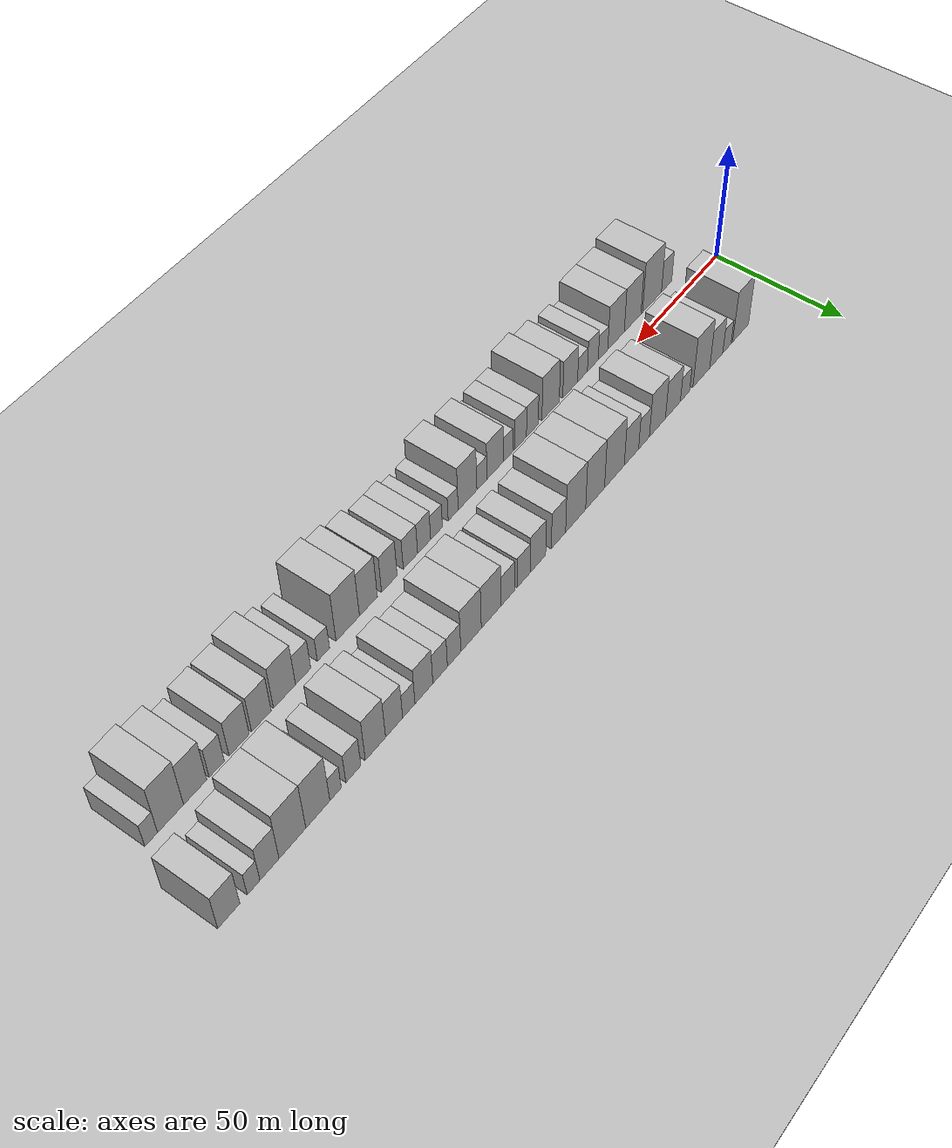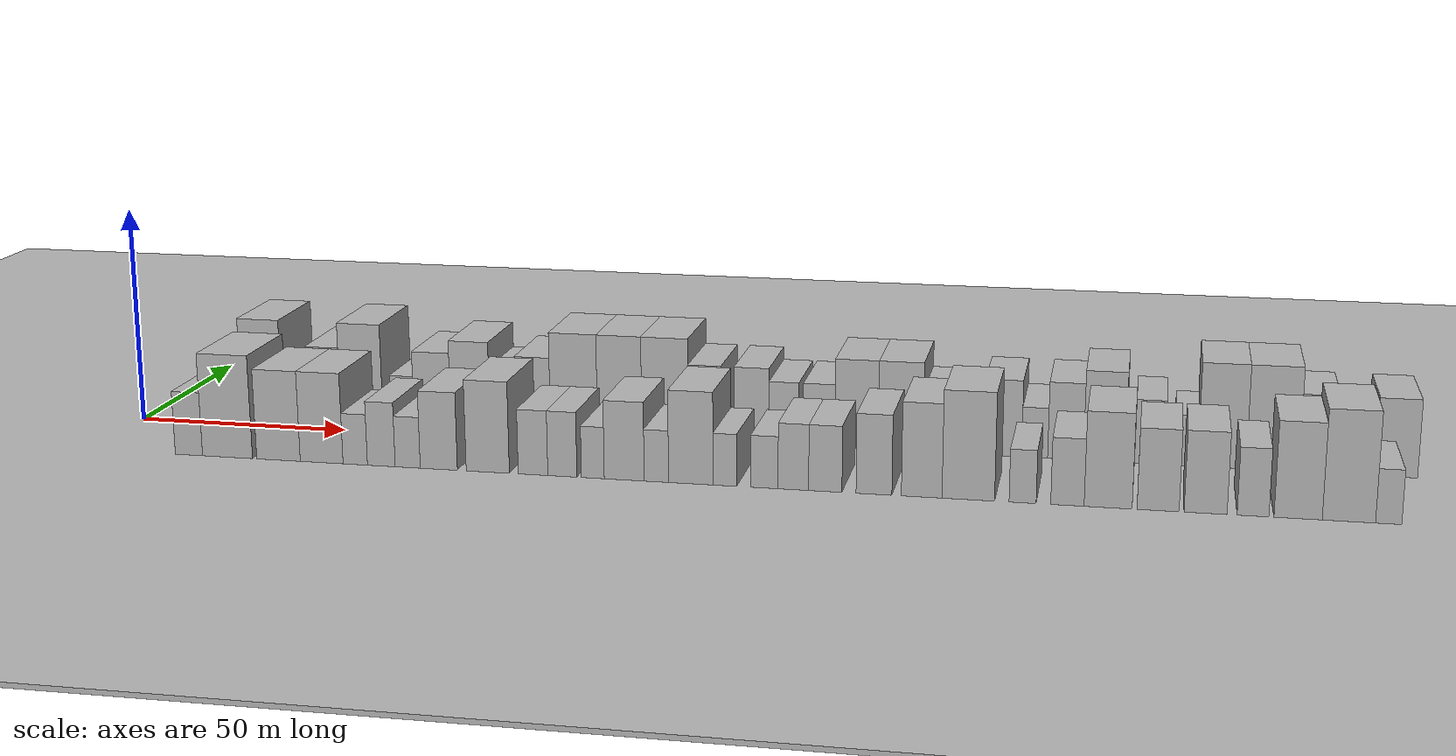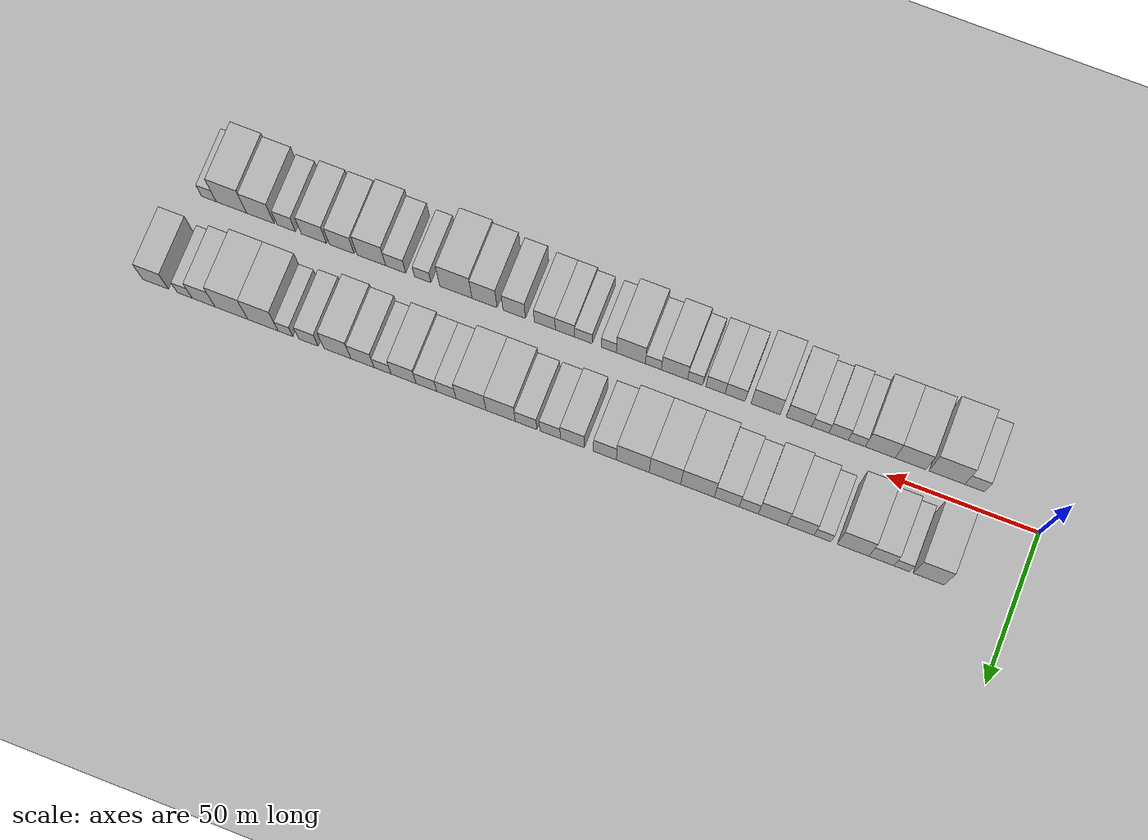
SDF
<?xml version="1.0" encoding="utf-8"?>

<sdf version="1.6">

   <world name="default">

      <gui fullscreen="0">

         <camera name="user_camera">

            <pose>-15 0 4.57585 0 0 0</pose>

            <view_controller>orbit</view_controller>

         </camera>

      </gui>

      <scene>

         <sky>

           <clouds>

             <speed>12</speed>

           </clouds>

         </sky>

         <ambient>0.4 0.4 0.4 1</ambient>

         <background>0.7 0.7 0.7 1</background>

         <shadows>1</shadows>

      </scene>

      <gravity>0 0 -9.8066</gravity>

      <magnetic_field>6e-06 2.3e-05 -4.2e-05</magnetic_field>

      <physics default="0" name="default_physics" type="ode">

         <ode>

            <solver>

               <type>quick</type>

               <iters>10</iters>

               <sor>1.0</sor>

               <use_dynamic_moi_rescaling>0</use_dynamic_moi_rescaling>

            </solver>

            <constraints>

               <cfm>0</cfm>

               <erp>0.2</erp>

               <contact_max_correcting_vel>100</contact_max_correcting_vel>

               <contact_surface_layer>0.001</contact_surface_layer>

            </constraints>

         </ode>

         <max_step_size>0.004</max_step_size>

         <real_time_factor>1</real_time_factor>

         <real_time_update_rate>250</real_time_update_rate>

      </physics>

      <light name="sun" type="directional">

         <cast_shadows>1</cast_shadows>

         <pose>0 0 10 0 0 0</pose>

         <diffuse>0.8 0.8 0.8 1</diffuse>

         <specular>0.2 0.2 0.2 1</specular>

         <attenuation>

            <range>1000</range>

            <constant>0.9</constant>

            <linear>0.01</linear>

            <quadratic>0.001</quadratic>

         </attenuation>

         <direction>-0.5 0.1 -0.9</direction>

      </light>

      <include>

         <name>ground_plane_1</name>

         <uri>model://HANNAS_ground_plane</uri>

         <pose>0 0 0  0 0 0</pose>

      </include>

      <include>

         <name>ground_plane_2</name>

         <uri>model://HANNAS_ground_plane</uri>

         <pose>100 0 0  0 0 0</pose>

      </include>

      <model name="building_1">

         <static>1</static>

         <pose frame="">27.0947 16.0000 0 0.000000 0.000000 1.570796</pose>

         <link name="link">

            <pose frame="">0 0 12.00 0 0 0</pose>

            <collision name="collision">

               <geometry>

                  <box>

                     <size>20.0000 10.1894 24.0000</size>

                  </box>

               </geometry>

               <max_contacts>10</max_contacts>

               <surface>

                  <contact>

                     <ode/>

                  </contact>

                  <bounce/>

                  <friction>

                     <torsional>

                        <ode/>

                     </torsional>

                     <ode/>

                  </friction>

               </surface>

            </collision>

            <visual name="visual">

               <cast_shadows>0</cast_shadows>

               <geometry>

                  <box>

                     <size>20.0000 10.1894 24.0000</size>

                  </box>

               </geometry>

               <material>

                  <script>

                     <uri>model://HANNAS_wall/materials/scripts</uri>

                     <uri>model://HANNAS_wall/materials/textures</uri>

                     <name>vrc/HANNAS_wall</name>

                  </script>

               </material>

            </visual>

            <self_collide>0</self_collide>

            <enable_wind>0</enable_wind>

            <kinematic>0</kinematic>

         </link>

      </model>

      <model name="building_2">

         <static>1</static>

         <pose frame="">35.8412 16.0000 0 0.000000 0.000000 1.570796</pose>

         <link name="link">

            <pose frame="">0 0 6.00 0 0 0</pose>

            <collision name="collision">

               <geometry>

                  <box>

                     <size>20.0000 5.3035 12.0000</size>

                  </box>

               </geometry>

               <max_contacts>10</max_contacts>

               <surface>

                  <contact>

                     <ode/>

                  </contact>

                  <bounce/>

                  <friction>

                     <torsional>

                        <ode/>

                     </torsional>

                     <ode/>

                  </friction>

               </surface>

            </collision>

            <visual name="visual">

               <cast_shadows>0</cast_shadows>

               <geometry>

                  <box>

                     <size>20.0000 5.3035 12.0000</size>

                  </box>

               </geometry>

               <material>

                  <script>

                     <uri>model://HANNAS_wall/materials/scripts</uri>

                     <uri>model://HANNAS_wall/materials/textures</uri>

                     <name>vrc/HANNAS_wall</name>

                  </script>

               </material>

            </visual>

            <self_collide>0</self_collide>

            <enable_wind>0</enable_wind>

            <kinematic>0</kinematic>

         </link>

      </model>

      <model name="building_3">

         <static>1</static>

         <pose frame="">42.5655 16.0000 0 0.000000 0.000000 1.570796</pose>

         <link name="link">

            <pose frame="">0 0 9.00 0 0 0</pose>

            <collision name="collision">

               <geometry>

                  <box>

                     <size>20.0000 8.1453 18.0000</size>

                  </box>

               </geometry>

               <max_contacts>10</max_contacts>

               <surface>

                  <contact>

                     <ode/>

                  </contact>

                  <bounce/>

                  <friction>

                     <torsional>

                        <ode/>

                     </torsional>

                     <ode/>

                  </friction>

               </surface>

            </collision>

            <visual name="visual">

               <cast_shadows>0</cast_shadows>

               <geometry>

                  <box>

                     <size>20.0000 8.1453 18.0000</size>

                  </box>

               </geometry>

               <material>

                  <script>

                     <uri>model://HANNAS_wall/materials/scripts</uri>

                     <uri>model://HANNAS_wall/materials/textures</uri>

                     <name>vrc/HANNAS_wall</name>

                  </script>

               </material>

            </visual>

            <self_collide>0</self_collide>

            <enable_wind>0</enable_wind>

            <kinematic>0</kinematic>

         </link>

      </model>

      <model name="building_4">

         <static>1</static>

         <pose frame="">51.8366 16.0000 0 0.000000 0.000000 1.570796</pose>

         <link name="link">

            <pose frame="">0 0 12.00 0 0 0</pose>

            <collision name="collision">

               <geometry>

                  <box>

                     <size>20.0000 10.3967 24.0000</size>

                  </box>

               </geometry>

               <max_contacts>10</max_contacts>

               <surface>

                  <contact>

                     <ode/>

                  </contact>

                  <bounce/>

                  <friction>

                     <torsional>

                        <ode/>

                     </torsional>

                     <ode/>

                  </friction>

               </surface>

            </collision>

            <visual name="visual">

               <cast_shadows>0</cast_shadows>

               <geometry>

                  <box>

                     <size>20.0000 10.3967 24.0000</size>

                  </box>

               </geometry>

               <material>

                  <script>

                     <uri>model://HANNAS_wall/materials/scripts</uri>

                     <uri>model://HANNAS_wall/materials/textures</uri>

                     <name>vrc/HANNAS_wall</name>

                  </script>

               </material>

            </visual>

            <self_collide>0</self_collide>

            <enable_wind>0</enable_wind>

            <kinematic>0</kinematic>

         </link>

      </model>

      <model name="building_5">

         <static>1</static>

         <pose frame="">61.8363 16.0000 0 0.000000 0.000000 1.570796</pose>

         <link name="link">

            <pose frame="">0 0 6.00 0 0 0</pose>

            <collision name="collision">

               <geometry>

                  <box>

                     <size>20.0000 5.6027 12.0000</size>

                  </box>

               </geometry>

               <max_contacts>10</max_contacts>

               <surface>

                  <contact>

                     <ode/>

                  </contact>

                  <bounce/>

                  <friction>

                     <torsional>

                        <ode/>

                     </torsional>

                     <ode/>

                  </friction>

               </surface>

            </collision>

            <visual name="visual">

               <cast_shadows>0</cast_shadows>

               <geometry>

                  <box>

                     <size>20.0000 5.6027 12.0000</size>

                  </box>

               </geometry>

               <material>

                  <script>

                     <uri>model://HANNAS_wall/materials/scripts</uri>

                     <uri>model://HANNAS_wall/materials/textures</uri>

                     <name>vrc/HANNAS_wall</name>

                  </script>

               </material>

            </visual>

            <self_collide>0</self_collide>

            <enable_wind>0</enable_wind>

            <kinematic>0</kinematic>

         </link>

      </model>

      <model name="building_6">

         <static>1</static>

         <pose frame="">69.1210 16.0000 0 0.000000 0.000000 1.570796</pose>

         <link name="link">

            <pose frame="">0 0 9.00 0 0 0</pose>

            <collision name="collision">

               <geometry>

                  <box>

                     <size>20.0000 8.9667 18.0000</size>

                  </box>

               </geometry>

               <max_contacts>10</max_contacts>

               <surface>

                  <contact>

                     <ode/>

                  </contact>

                  <bounce/>

                  <friction>

                     <torsional>

                        <ode/>

                     </torsional>

                     <ode/>

                  </friction>

               </surface>

            </collision>

            <visual name="visual">

               <cast_shadows>0</cast_shadows>

               <geometry>

                  <box>

                     <size>20.0000 8.9667 18.0000</size>

                  </box>

               </geometry>

               <material>

                  <script>

                     <uri>model://HANNAS_wall/materials/scripts</uri>

                     <uri>model://HANNAS_wall/materials/textures</uri>

                     <name>vrc/HANNAS_wall</name>

                  </script>

               </material>

            </visual>

            <self_collide>0</self_collide>

            <enable_wind>0</enable_wind>

            <kinematic>0</kinematic>

         </link>

      </model>

      <model name="building_7">

         <static>1</static>

         <pose frame="">78.3468 16.0000 0 0.000000 0.000000 1.570796</pose>

         <link name="link">

            <pose frame="">0 0 10.50 0 0 0</pose>

            <collision name="collision">

               <geometry>

                  <box>

                     <size>20.0000 9.4850 21.0000</size>

                  </box>

               </geometry>

               <max_contacts>10</max_contacts>

               <surface>

                  <contact>

                     <ode/>

                  </contact>

                  <bounce/>

                  <friction>

                     <torsional>

                        <ode/>

                     </torsional>

                     <ode/>

                  </friction>

               </surface>

            </collision>

            <visual name="visual">

               <cast_shadows>0</cast_shadows>

               <geometry>

                  <box>

                     <size>20.0000 9.4850 21.0000</size>

                  </box>

               </geometry>

               <material>

                  <script>

                     <uri>model://HANNAS_wall/materials/scripts</uri>

                     <uri>model://HANNAS_wall/materials/textures</uri>

                     <name>vrc/HANNAS_wall</name>

                  </script>

               </material>

            </visual>

            <self_collide>0</self_collide>

            <enable_wind>0</enable_wind>

            <kinematic>0</kinematic>

         </link>

      </model>

      <model name="building_8">

         <static>1</static>

         <pose frame="">86.2130 16.0000 0 0.000000 0.000000 1.570796</pose>

         <link name="link">

            <pose frame="">0 0 7.50 0 0 0</pose>

            <collision name="collision">

               <geometry>

                  <box>

                     <size>20.0000 6.2475 15.0000</size>

                  </box>

               </geometry>

               <max_contacts>10</max_contacts>

               <surface>

                  <contact>

                     <ode/>

                  </contact>

                  <bounce/>

                  <friction>

                     <torsional>

                        <ode/>

                     </torsional>

                     <ode/>

                  </friction>

               </surface>

            </collision>

            <visual name="visual">

               <cast_shadows>0</cast_shadows>

               <geometry>

                  <box>

                     <size>20.0000 6.2475 15.0000</size>

                  </box>

               </geometry>

               <material>

                  <script>

                     <uri>model://HANNAS_wall/materials/scripts</uri>

                     <uri>model://HANNAS_wall/materials/textures</uri>

                     <name>vrc/HANNAS_wall</name>

                  </script>

               </material>

            </visual>

            <self_collide>0</self_collide>

            <enable_wind>0</enable_wind>

            <kinematic>0</kinematic>

         </link>

      </model>

      <model name="building_9">

         <static>1</static>

         <pose frame="">93.4682 16.0000 0 0.000000 0.000000 1.570796</pose>

         <link name="link">

            <pose frame="">0 0 9.00 0 0 0</pose>

            <collision name="collision">

               <geometry>

                  <box>

                     <size>20.0000 8.2628 18.0000</size>

                  </box>

               </geometry>

               <max_contacts>10</max_contacts>

               <surface>

                  <contact>

                     <ode/>

                  </contact>

                  <bounce/>

                  <friction>

                     <torsional>

                        <ode/>

                     </torsional>

                     <ode/>

                  </friction>

               </surface>

            </collision>

            <visual name="visual">

               <cast_shadows>0</cast_shadows>

               <geometry>

                  <box>

                     <size>20.0000 8.2628 18.0000</size>

                  </box>

               </geometry>

               <material>

                  <script>

                     <uri>model://HANNAS_wall/materials/scripts</uri>

                     <uri>model://HANNAS_wall/materials/textures</uri>

                     <name>vrc/HANNAS_wall</name>

                  </script>

               </material>

            </visual>

            <self_collide>0</self_collide>

            <enable_wind>0</enable_wind>

            <kinematic>0</kinematic>

         </link>

      </model>

      <model name="building_10">

         <static>1</static>

         <pose frame="">103.1836 16.0000 0 0.000000 0.000000 1.570796</pose>

         <link name="link">

            <pose frame="">0 0 12.00 0 0 0</pose>

            <collision name="collision">

               <geometry>

                  <box>

                     <size>20.0000 11.1680 24.0000</size>

                  </box>

               </geometry>

               <max_contacts>10</max_contacts>

               <surface>

                  <contact>

                     <ode/>

                  </contact>

                  <bounce/>

                  <friction>

                     <torsional>

                        <ode/>

                     </torsional>

                     <ode/>

                  </friction>

               </surface>

            </collision>

            <visual name="visual">

               <cast_shadows>0</cast_shadows>

               <geometry>

                  <box>

                     <size>20.0000 11.1680 24.0000</size>

                  </box>

               </geometry>

               <material>

                  <script>

                     <uri>model://HANNAS_wall/materials/scripts</uri>

                     <uri>model://HANNAS_wall/materials/textures</uri>

                     <name>vrc/HANNAS_wall</name>

                  </script>

               </material>

            </visual>

            <self_collide>0</self_collide>

            <enable_wind>0</enable_wind>

            <kinematic>0</kinematic>

         </link>

      </model>

      <model name="building_11">

         <static>1</static>

         <pose frame="">114.0041 16.0000 0 0.000000 0.000000 1.570796</pose>

         <link name="link">

            <pose frame="">0 0 12.00 0 0 0</pose>

            <collision name="collision">

               <geometry>

                  <box>

                     <size>20.0000 10.4730 24.0000</size>

                  </box>

               </geometry>

               <max_contacts>10</max_contacts>

               <surface>

                  <contact>

                     <ode/>

                  </contact>

                  <bounce/>

                  <friction>

                     <torsional>

                        <ode/>

                     </torsional>

                     <ode/>

                  </friction>

               </surface>

            </collision>

            <visual name="visual">

               <cast_shadows>0</cast_shadows>

               <geometry>

                  <box>

                     <size>20.0000 10.4730 24.0000</size>

                  </box>

               </geometry>

               <material>

                  <script>

                     <uri>model://HANNAS_wall/materials/scripts</uri>

                     <uri>model://HANNAS_wall/materials/textures</uri>

                     <name>vrc/HANNAS_wall</name>

                  </script>

               </material>

            </visual>

            <self_collide>0</self_collide>

            <enable_wind>0</enable_wind>

            <kinematic>0</kinematic>

         </link>

      </model>

      <model name="building_12">

         <static>1</static>

         <pose frame="">124.6937 16.0000 0 0.000000 0.000000 1.570796</pose>

         <link name="link">

            <pose frame="">0 0 12.00 0 0 0</pose>

            <collision name="collision">

               <geometry>

                  <box>

                     <size>20.0000 10.9062 24.0000</size>

                  </box>

               </geometry>

               <max_contacts>10</max_contacts>

               <surface>

                  <contact>

                     <ode/>

                  </contact>

                  <bounce/>

                  <friction>

                     <torsional>

                        <ode/>

                     </torsional>

                     <ode/>

                  </friction>

               </surface>

            </collision>

            <visual name="visual">

               <cast_shadows>0</cast_shadows>

               <geometry>

                  <box>

                     <size>20.0000 10.9062 24.0000</size>

                  </box>

               </geometry>

               <material>

                  <script>

                     <uri>model://HANNAS_wall/materials/scripts</uri>

                     <uri>model://HANNAS_wall/materials/textures</uri>

                     <name>vrc/HANNAS_wall</name>

                  </script>

               </material>

            </visual>

            <self_collide>0</self_collide>

            <enable_wind>0</enable_wind>

            <kinematic>0</kinematic>

         </link>

      </model>

      <model name="building_13">

         <static>1</static>

         <pose frame="">133.9658 16.0000 0 0.000000 0.000000 1.570796</pose>

         <link name="link">

            <pose frame="">0 0 9.00 0 0 0</pose>

            <collision name="collision">

               <geometry>

                  <box>

                     <size>20.0000 7.6379 18.0000</size>

                  </box>

               </geometry>

               <max_contacts>10</max_contacts>

               <surface>

                  <contact>

                     <ode/>

                  </contact>

                  <bounce/>

                  <friction>

                     <torsional>

                        <ode/>

                     </torsional>

                     <ode/>

                  </friction>

               </surface>

            </collision>

            <visual name="visual">

               <cast_shadows>0</cast_shadows>

               <geometry>

                  <box>

                     <size>20.0000 7.6379 18.0000</size>

                  </box>

               </geometry>

               <material>

                  <script>

                     <uri>model://HANNAS_wall/materials/scripts</uri>

                     <uri>model://HANNAS_wall/materials/textures</uri>

                     <name>vrc/HANNAS_wall</name>

                  </script>

               </material>

            </visual>

            <self_collide>0</self_collide>

            <enable_wind>0</enable_wind>

            <kinematic>0</kinematic>

         </link>

      </model>

      <model name="building_14">

         <static>1</static>

         <pose frame="">144.8088 16.0000 0 0.000000 0.000000 1.570796</pose>

         <link name="link">

            <pose frame="">0 0 9.00 0 0 0</pose>

            <collision name="collision">

               <geometry>

                  <box>

                     <size>20.0000 8.0482 18.0000</size>

                  </box>

               </geometry>

               <max_contacts>10</max_contacts>

               <surface>

                  <contact>

                     <ode/>

                  </contact>

                  <bounce/>

                  <friction>

                     <torsional>

                        <ode/>

                     </torsional>

                     <ode/>

                  </friction>

               </surface>

            </collision>

            <visual name="visual">

               <cast_shadows>0</cast_shadows>

               <geometry>

                  <box>

                     <size>20.0000 8.0482 18.0000</size>

                  </box>

               </geometry>

               <material>

                  <script>

                     <uri>model://HANNAS_wall/materials/scripts</uri>

                     <uri>model://HANNAS_wall/materials/textures</uri>

                     <name>vrc/HANNAS_wall</name>

                  </script>

               </material>

            </visual>

            <self_collide>0</self_collide>

            <enable_wind>0</enable_wind>

            <kinematic>0</kinematic>

         </link>

      </model>

      <model name="building_15">

         <static>1</static>

         <pose frame="">152.2666 16.0000 0 0.000000 0.000000 1.570796</pose>

         <link name="link">

            <pose frame="">0 0 7.50 0 0 0</pose>

            <collision name="collision">

               <geometry>

                  <box>

                     <size>20.0000 6.8674 15.0000</size>

                  </box>

               </geometry>

               <max_contacts>10</max_contacts>

               <surface>

                  <contact>

                     <ode/>

                  </contact>

                  <bounce/>

                  <friction>

                     <torsional>

                        <ode/>

                     </torsional>

                     <ode/>

                  </friction>

               </surface>

            </collision>

            <visual name="visual">

               <cast_shadows>0</cast_shadows>

               <geometry>

                  <box>

                     <size>20.0000 6.8674 15.0000</size>

                  </box>

               </geometry>

               <material>

                  <script>

                     <uri>model://HANNAS_wall/materials/scripts</uri>

                     <uri>model://HANNAS_wall/materials/textures</uri>

                     <name>vrc/HANNAS_wall</name>

                  </script>

               </material>

            </visual>

            <self_collide>0</self_collide>

            <enable_wind>0</enable_wind>

            <kinematic>0</kinematic>

         </link>

      </model>

      <model name="building_16">

         <static>1</static>

         <pose frame="">160.3227 16.0000 0 0.000000 0.000000 1.570796</pose>

         <link name="link">

            <pose frame="">0 0 7.50 0 0 0</pose>

            <collision name="collision">

               <geometry>

                  <box>

                     <size>20.0000 7.2447 15.0000</size>

                  </box>

               </geometry>

               <max_contacts>10</max_contacts>

               <surface>

                  <contact>

                     <ode/>

                  </contact>

                  <bounce/>

                  <friction>

                     <torsional>

                        <ode/>

                     </torsional>

                     <ode/>

                  </friction>

               </surface>

            </collision>

            <visual name="visual">

               <cast_shadows>0</cast_shadows>

               <geometry>

                  <box>

                     <size>20.0000 7.2447 15.0000</size>

                  </box>

               </geometry>

               <material>

                  <script>

                     <uri>model://HANNAS_wall/materials/scripts</uri>

                     <uri>model://HANNAS_wall/materials/textures</uri>

                     <name>vrc/HANNAS_wall</name>

                  </script>

               </material>

            </visual>

            <self_collide>0</self_collide>

            <enable_wind>0</enable_wind>

            <kinematic>0</kinematic>

         </link>

      </model>

      <model name="building_17">

         <static>1</static>

         <pose frame="">168.8690 16.0000 0 0.000000 0.000000 1.570796</pose>

         <link name="link">

            <pose frame="">0 0 10.50 0 0 0</pose>

            <collision name="collision">

               <geometry>

                  <box>

                     <size>20.0000 9.8481 21.0000</size>

                  </box>

               </geometry>

               <max_contacts>10</max_contacts>

               <surface>

                  <contact>

                     <ode/>

                  </contact>

                  <bounce/>

                  <friction>

                     <torsional>

                        <ode/>

                     </torsional>

                     <ode/>

                  </friction>

               </surface>

            </collision>

            <visual name="visual">

               <cast_shadows>0</cast_shadows>

               <geometry>

                  <box>

                     <size>20.0000 9.8481 21.0000</size>

                  </box>

               </geometry>

               <material>

                  <script>

                     <uri>model://HANNAS_wall/materials/scripts</uri>

                     <uri>model://HANNAS_wall/materials/textures</uri>

                     <name>vrc/HANNAS_wall</name>

                  </script>

               </material>

            </visual>

            <self_collide>0</self_collide>

            <enable_wind>0</enable_wind>

            <kinematic>0</kinematic>

         </link>

      </model>

      <model name="building_18">

         <static>1</static>

         <pose frame="">178.8394 16.0000 0 0.000000 0.000000 1.570796</pose>

         <link name="link">

            <pose frame="">0 0 10.50 0 0 0</pose>

            <collision name="collision">

               <geometry>

                  <box>

                     <size>20.0000 10.0925 21.0000</size>

                  </box>

               </geometry>

               <max_contacts>10</max_contacts>

               <surface>

                  <contact>

                     <ode/>

                  </contact>

                  <bounce/>

                  <friction>

                     <torsional>

                        <ode/>

                     </torsional>

                     <ode/>

                  </friction>

               </surface>

            </collision>

            <visual name="visual">

               <cast_shadows>0</cast_shadows>

               <geometry>

                  <box>

                     <size>20.0000 10.0925 21.0000</size>

                  </box>

               </geometry>

               <material>

                  <script>

                     <uri>model://HANNAS_wall/materials/scripts</uri>

                     <uri>model://HANNAS_wall/materials/textures</uri>

                     <name>vrc/HANNAS_wall</name>

                  </script>

               </material>

            </visual>

            <self_collide>0</self_collide>

            <enable_wind>0</enable_wind>

            <kinematic>0</kinematic>

         </link>

      </model>

      <model name="building_19">

         <static>1</static>

         <pose frame="">187.1426 16.0000 0 0.000000 0.000000 1.570796</pose>

         <link name="link">

            <pose frame="">0 0 7.50 0 0 0</pose>

            <collision name="collision">

               <geometry>

                  <box>

                     <size>20.0000 6.5140 15.0000</size>

                  </box>

               </geometry>

               <max_contacts>10</max_contacts>

               <surface>

                  <contact>

                     <ode/>

                  </contact>

                  <bounce/>

                  <friction>

                     <torsional>

                        <ode/>

                     </torsional>

                     <ode/>

                  </friction>

               </surface>

            </collision>

            <visual name="visual">

               <cast_shadows>0</cast_shadows>

               <geometry>

                  <box>

                     <size>20.0000 6.5140 15.0000</size>

                  </box>

               </geometry>

               <material>

                  <script>

                     <uri>model://HANNAS_wall/materials/scripts</uri>

                     <uri>model://HANNAS_wall/materials/textures</uri>

                     <name>vrc/HANNAS_wall</name>

                  </script>

               </material>

            </visual>

            <self_collide>0</self_collide>

            <enable_wind>0</enable_wind>

            <kinematic>0</kinematic>

         </link>

      </model>

      <model name="building_20">

         <static>1</static>

         <pose frame="">193.8943 16.0000 0 0.000000 0.000000 1.570796</pose>

         <link name="link">

            <pose frame="">0 0 7.50 0 0 0</pose>

            <collision name="collision">

               <geometry>

                  <box>

                     <size>20.0000 6.9893 15.0000</size>

                  </box>

               </geometry>

               <max_contacts>10</max_contacts>

               <surface>

                  <contact>

                     <ode/>

                  </contact>

                  <bounce/>

                  <friction>

                     <torsional>

                        <ode/>

                     </torsional>

                     <ode/>

                  </friction>

               </surface>

            </collision>

            <visual name="visual">

               <cast_shadows>0</cast_shadows>

               <geometry>

                  <box>

                     <size>20.0000 6.9893 15.0000</size>

                  </box>

               </geometry>

               <material>

                  <script>

                     <uri>model://HANNAS_wall/materials/scripts</uri>

                     <uri>model://HANNAS_wall/materials/textures</uri>

                     <name>vrc/HANNAS_wall</name>

                  </script>

               </material>

            </visual>

            <self_collide>0</self_collide>

            <enable_wind>0</enable_wind>

            <kinematic>0</kinematic>

         </link>

      </model>

      <model name="building_21">

         <static>1</static>

         <pose frame="">201.6064 16.0000 0 0.000000 0.000000 1.570796</pose>

         <link name="link">

            <pose frame="">0 0 9.00 0 0 0</pose>

            <collision name="collision">

               <geometry>

                  <box>

                     <size>20.0000 8.4348 18.0000</size>

                  </box>

               </geometry>

               <max_contacts>10</max_contacts>

               <surface>

                  <contact>

                     <ode/>

                  </contact>

                  <bounce/>

                  <friction>

                     <torsional>

                        <ode/>

                     </torsional>

                     <ode/>

                  </friction>

               </surface>

            </collision>

            <visual name="visual">

               <cast_shadows>0</cast_shadows>

               <geometry>

                  <box>

                     <size>20.0000 8.4348 18.0000</size>

                  </box>

               </geometry>

               <material>

                  <script>

                     <uri>model://HANNAS_wall/materials/scripts</uri>

                     <uri>model://HANNAS_wall/materials/textures</uri>

                     <name>vrc/HANNAS_wall</name>

                  </script>

               </material>

            </visual>

            <self_collide>0</self_collide>

            <enable_wind>0</enable_wind>

            <kinematic>0</kinematic>

         </link>

      </model>

      <model name="building_22">

         <static>1</static>

         <pose frame="">208.6975 16.0000 0 0.000000 0.000000 1.570796</pose>

         <link name="link">

            <pose frame="">0 0 6.00 0 0 0</pose>

            <collision name="collision">

               <geometry>

                  <box>

                     <size>20.0000 5.7476 12.0000</size>

                  </box>

               </geometry>

               <max_contacts>10</max_contacts>

               <surface>

                  <contact>

                     <ode/>

                  </contact>

                  <bounce/>

                  <friction>

                     <torsional>

                        <ode/>

                     </torsional>

                     <ode/>

                  </friction>

               </surface>

            </collision>

            <visual name="visual">

               <cast_shadows>0</cast_shadows>

               <geometry>

                  <box>

                     <size>20.0000 5.7476 12.0000</size>

                  </box>

               </geometry>

               <material>

                  <script>

                     <uri>model://HANNAS_wall/materials/scripts</uri>

                     <uri>model://HANNAS_wall/materials/textures</uri>

                     <name>vrc/HANNAS_wall</name>

                  </script>

               </material>

            </visual>

            <self_collide>0</self_collide>

            <enable_wind>0</enable_wind>

            <kinematic>0</kinematic>

         </link>

      </model>

      <model name="building_23">

         <static>1</static>

         <pose frame="">215.4976 16.0000 0 0.000000 0.000000 1.570796</pose>

         <link name="link">

            <pose frame="">0 0 9.00 0 0 0</pose>

            <collision name="collision">

               <geometry>

                  <box>

                     <size>20.0000 7.8526 18.0000</size>

                  </box>

               </geometry>

               <max_contacts>10</max_contacts>

               <surface>

                  <contact>

                     <ode/>

                  </contact>

                  <bounce/>

                  <friction>

                     <torsional>

                        <ode/>

                     </torsional>

                     <ode/>

                  </friction>

               </surface>

            </collision>

            <visual name="visual">

               <cast_shadows>0</cast_shadows>

               <geometry>

                  <box>

                     <size>20.0000 7.8526 18.0000</size>

                  </box>

               </geometry>

               <material>

                  <script>

                     <uri>model://HANNAS_wall/materials/scripts</uri>

                     <uri>model://HANNAS_wall/materials/textures</uri>

                     <name>vrc/HANNAS_wall</name>

                  </script>

               </material>

            </visual>

            <self_collide>0</self_collide>

            <enable_wind>0</enable_wind>

            <kinematic>0</kinematic>

         </link>

      </model>

      <model name="building_24">

         <static>1</static>

         <pose frame="">224.0036 16.0000 0 0.000000 0.000000 1.570796</pose>

         <link name="link">

            <pose frame="">0 0 10.50 0 0 0</pose>

            <collision name="collision">

               <geometry>

                  <box>

                     <size>20.0000 9.1593 21.0000</size>

                  </box>

               </geometry>

               <max_contacts>10</max_contacts>

               <surface>

                  <contact>

                     <ode/>

                  </contact>

                  <bounce/>

                  <friction>

                     <torsional>

                        <ode/>

                     </torsional>

                     <ode/>

                  </friction>

               </surface>

            </collision>

            <visual name="visual">

               <cast_shadows>0</cast_shadows>

               <geometry>

                  <box>

                     <size>20.0000 9.1593 21.0000</size>

                  </box>

               </geometry>

               <material>

                  <script>

                     <uri>model://HANNAS_wall/materials/scripts</uri>

                     <uri>model://HANNAS_wall/materials/textures</uri>

                     <name>vrc/HANNAS_wall</name>

                  </script>

               </material>

            </visual>

            <self_collide>0</self_collide>

            <enable_wind>0</enable_wind>

            <kinematic>0</kinematic>

         </link>

      </model>

      <model name="building_25">

         <static>1</static>

         <pose frame="">233.9026 16.0000 0 0.000000 0.000000 1.570796</pose>

         <link name="link">

            <pose frame="">0 0 7.50 0 0 0</pose>

            <collision name="collision">

               <geometry>

                  <box>

                     <size>20.0000 6.6388 15.0000</size>

                  </box>

               </geometry>

               <max_contacts>10</max_contacts>

               <surface>

                  <contact>

                     <ode/>

                  </contact>

                  <bounce/>

                  <friction>

                     <torsional>

                        <ode/>

                     </torsional>

                     <ode/>

                  </friction>

               </surface>

            </collision>

            <visual name="visual">

               <cast_shadows>0</cast_shadows>

               <geometry>

                  <box>

                     <size>20.0000 6.6388 15.0000</size>

                  </box>

               </geometry>

               <material>

                  <script>

                     <uri>model://HANNAS_wall/materials/scripts</uri>

                     <uri>model://HANNAS_wall/materials/textures</uri>

                     <name>vrc/HANNAS_wall</name>

                  </script>

               </material>

            </visual>

            <self_collide>0</self_collide>

            <enable_wind>0</enable_wind>

            <kinematic>0</kinematic>

         </link>

      </model>

      <model name="building_26">

         <static>1</static>

         <pose frame="">241.7194 16.0000 0 0.000000 0.000000 1.570796</pose>

         <link name="link">

            <pose frame="">0 0 6.00 0 0 0</pose>

            <collision name="collision">

               <geometry>

                  <box>

                     <size>20.0000 4.9949 12.0000</size>

                  </box>

               </geometry>

               <max_contacts>10</max_contacts>

               <surface>

                  <contact>

                     <ode/>

                  </contact>

                  <bounce/>

                  <friction>

                     <torsional>

                        <ode/>

                     </torsional>

                     <ode/>

                  </friction>

               </surface>

            </collision>

            <visual name="visual">

               <cast_shadows>0</cast_shadows>

               <geometry>

                  <box>

                     <size>20.0000 4.9949 12.0000</size>

                  </box>

               </geometry>

               <material>

                  <script>

                     <uri>model://HANNAS_wall/materials/scripts</uri>

                     <uri>model://HANNAS_wall/materials/textures</uri>

                     <name>vrc/HANNAS_wall</name>

                  </script>

               </material>

            </visual>

            <self_collide>0</self_collide>

            <enable_wind>0</enable_wind>

            <kinematic>0</kinematic>

         </link>

      </model>

      <model name="building_27">

         <static>1</static>

         <pose frame="">249.4004 16.0000 0 0.000000 0.000000 1.570796</pose>

         <link name="link">

            <pose frame="">0 0 12.00 0 0 0</pose>

            <collision name="collision">

               <geometry>

                  <box>

                     <size>20.0000 10.3670 24.0000</size>

                  </box>

               </geometry>

               <max_contacts>10</max_contacts>

               <surface>

                  <contact>

                     <ode/>

                  </contact>

                  <bounce/>

                  <friction>

                     <torsional>

                        <ode/>

                     </torsional>

                     <ode/>

                  </friction>

               </surface>

            </collision>

            <visual name="visual">

               <cast_shadows>0</cast_shadows>

               <geometry>

                  <box>

                     <size>20.0000 10.3670 24.0000</size>

                  </box>

               </geometry>

               <material>

                  <script>

                     <uri>model://HANNAS_wall/materials/scripts</uri>

                     <uri>model://HANNAS_wall/materials/textures</uri>

                     <name>vrc/HANNAS_wall</name>

                  </script>

               </material>

            </visual>

            <self_collide>0</self_collide>

            <enable_wind>0</enable_wind>

            <kinematic>0</kinematic>

         </link>

      </model>

      <model name="building_28">

         <static>1</static>

         <pose frame="">260.2053 16.0000 0 0.000000 0.000000 1.570796</pose>

         <link name="link">

            <pose frame="">0 0 12.00 0 0 0</pose>

            <collision name="collision">

               <geometry>

                  <box>

                     <size>20.0000 11.2428 24.0000</size>

                  </box>

               </geometry>

               <max_contacts>10</max_contacts>

               <surface>

                  <contact>

                     <ode/>

                  </contact>

                  <bounce/>

                  <friction>

                     <torsional>

                        <ode/>

                     </torsional>

                     <ode/>

                  </friction>

               </surface>

            </collision>

            <visual name="visual">

               <cast_shadows>0</cast_shadows>

               <geometry>

                  <box>

                     <size>20.0000 11.2428 24.0000</size>

                  </box>

               </geometry>

               <material>

                  <script>

                     <uri>model://HANNAS_wall/materials/scripts</uri>

                     <uri>model://HANNAS_wall/materials/textures</uri>

                     <name>vrc/HANNAS_wall</name>

                  </script>

               </material>

            </visual>

            <self_collide>0</self_collide>

            <enable_wind>0</enable_wind>

            <kinematic>0</kinematic>

         </link>

      </model>

      <model name="building_29">

         <static>1</static>

         <pose frame="">269.7765 16.0000 0 0.000000 0.000000 1.570796</pose>

         <link name="link">

            <pose frame="">0 0 9.00 0 0 0</pose>

            <collision name="collision">

               <geometry>

                  <box>

                     <size>20.0000 7.8995 18.0000</size>

                  </box>

               </geometry>

               <max_contacts>10</max_contacts>

               <surface>

                  <contact>

                     <ode/>

                  </contact>

                  <bounce/>

                  <friction>

                     <torsional>

                        <ode/>

                     </torsional>

                     <ode/>

                  </friction>

               </surface>

            </collision>

            <visual name="visual">

               <cast_shadows>0</cast_shadows>

               <geometry>

                  <box>

                     <size>20.0000 7.8995 18.0000</size>

                  </box>

               </geometry>

               <material>

                  <script>

                     <uri>model://HANNAS_wall/materials/scripts</uri>

                     <uri>model://HANNAS_wall/materials/textures</uri>

                     <name>vrc/HANNAS_wall</name>

                  </script>

               </material>

            </visual>

            <self_collide>0</self_collide>

            <enable_wind>0</enable_wind>

            <kinematic>0</kinematic>

         </link>

      </model>

      <model name="building_30">

         <static>1</static>

         <pose frame="">276.3027 16.0000 0 0.000000 0.000000 1.570796</pose>

         <link name="link">

            <pose frame="">0 0 6.00 0 0 0</pose>

            <collision name="collision">

               <geometry>

                  <box>

                     <size>20.0000 5.1528 12.0000</size>

                  </box>

               </geometry>

               <max_contacts>10</max_contacts>

               <surface>

                  <contact>

                     <ode/>

                  </contact>

                  <bounce/>

                  <friction>

                     <torsional>

                        <ode/>

                     </torsional>

                     <ode/>

                  </friction>

               </surface>

            </collision>

            <visual name="visual">

               <cast_shadows>0</cast_shadows>

               <geometry>

                  <box>

                     <size>20.0000 5.1528 12.0000</size>

                  </box>

               </geometry>

               <material>

                  <script>

                     <uri>model://HANNAS_wall/materials/scripts</uri>

                     <uri>model://HANNAS_wall/materials/textures</uri>

                     <name>vrc/HANNAS_wall</name>

                  </script>

               </material>

            </visual>

            <self_collide>0</self_collide>

            <enable_wind>0</enable_wind>

            <kinematic>0</kinematic>

         </link>

      </model>

      <model name="building_31">

         <static>1</static>

         <pose frame="">286.2934 16.0000 0 0.000000 0.000000 1.570796</pose>

         <link name="link">

            <pose frame="">0 0 9.00 0 0 0</pose>

            <collision name="collision">

               <geometry>

                  <box>

                     <size>20.0000 8.8286 18.0000</size>

                  </box>

               </geometry>

               <max_contacts>10</max_contacts>

               <surface>

                  <contact>

                     <ode/>

                  </contact>

                  <bounce/>

                  <friction>

                     <torsional>

                        <ode/>

                     </torsional>

                     <ode/>

                  </friction>

               </surface>

            </collision>

            <visual name="visual">

               <cast_shadows>0</cast_shadows>

               <geometry>

                  <box>

                     <size>20.0000 8.8286 18.0000</size>

                  </box>

               </geometry>

               <material>

                  <script>

                     <uri>model://HANNAS_wall/materials/scripts</uri>

                     <uri>model://HANNAS_wall/materials/textures</uri>

                     <name>vrc/HANNAS_wall</name>

                  </script>

               </material>

            </visual>

            <self_collide>0</self_collide>

            <enable_wind>0</enable_wind>

            <kinematic>0</kinematic>

         </link>

      </model>

      <model name="building_32">

         <static>1</static>

         <pose frame="">23.2325 -16.0000 0 0.000000 0.000000 1.570796</pose>

         <link name="link">

            <pose frame="">0 0 7.50 0 0 0</pose>

            <collision name="collision">

               <geometry>

                  <box>

                     <size>20.0000 6.4650 15.0000</size>

                  </box>

               </geometry>

               <max_contacts>10</max_contacts>

               <surface>

                  <contact>

                     <ode/>

                  </contact>

                  <bounce/>

                  <friction>

                     <torsional>

                        <ode/>

                     </torsional>

                     <ode/>

                  </friction>

               </surface>

            </collision>

            <visual name="visual">

               <cast_shadows>0</cast_shadows>

               <geometry>

                  <box>

                     <size>20.0000 6.4650 15.0000</size>

                  </box>

               </geometry>

               <material>

                  <script>

                     <uri>model://HANNAS_wall/materials/scripts</uri>

                     <uri>model://HANNAS_wall/materials/textures</uri>

                     <name>vrc/HANNAS_wall</name>

                  </script>

               </material>

            </visual>

            <self_collide>0</self_collide>

            <enable_wind>0</enable_wind>

            <kinematic>0</kinematic>

         </link>

      </model>

      <model name="building_33">

         <static>1</static>

         <pose frame="">32.3627 -16.0000 0 0.000000 0.000000 1.570796</pose>

         <link name="link">

            <pose frame="">0 0 12.00 0 0 0</pose>

            <collision name="collision">

               <geometry>

                  <box>

                     <size>20.0000 11.7952 24.0000</size>

                  </box>

               </geometry>

               <max_contacts>10</max_contacts>

               <surface>

                  <contact>

                     <ode/>

                  </contact>

                  <bounce/>

                  <friction>

                     <torsional>

                        <ode/>

                     </torsional>

                     <ode/>

                  </friction>

               </surface>

            </collision>

            <visual name="visual">

               <cast_shadows>0</cast_shadows>

               <geometry>

                  <box>

                     <size>20.0000 11.7952 24.0000</size>

                  </box>

               </geometry>

               <material>

                  <script>

                     <uri>model://HANNAS_wall/materials/scripts</uri>

                     <uri>model://HANNAS_wall/materials/textures</uri>

                     <name>vrc/HANNAS_wall</name>

                  </script>

               </material>

            </visual>

            <self_collide>0</self_collide>

            <enable_wind>0</enable_wind>

            <kinematic>0</kinematic>

         </link>

      </model>

      <model name="building_34">

         <static>1</static>

         <pose frame="">44.3522 -16.0000 0 0.000000 0.000000 1.570796</pose>

         <link name="link">

            <pose frame="">0 0 10.50 0 0 0</pose>

            <collision name="collision">

               <geometry>

                  <box>

                     <size>20.0000 10.1837 21.0000</size>

                  </box>

               </geometry>

               <max_contacts>10</max_contacts>

               <surface>

                  <contact>

                     <ode/>

                  </contact>

                  <bounce/>

                  <friction>

                     <torsional>

                        <ode/>

                     </torsional>

                     <ode/>

                  </friction>

               </surface>

            </collision>

            <visual name="visual">

               <cast_shadows>0</cast_shadows>

               <geometry>

                  <box>

                     <size>20.0000 10.1837 21.0000</size>

                  </box>

               </geometry>

               <material>

                  <script>

                     <uri>model://HANNAS_wall/materials/scripts</uri>

                     <uri>model://HANNAS_wall/materials/textures</uri>

                     <name>vrc/HANNAS_wall</name>

                  </script>

               </material>

            </visual>

            <self_collide>0</self_collide>

            <enable_wind>0</enable_wind>

            <kinematic>0</kinematic>

         </link>

      </model>

      <model name="building_35">

         <static>1</static>

         <pose frame="">54.4142 -16.0000 0 0.000000 0.000000 1.570796</pose>

         <link name="link">

            <pose frame="">0 0 10.50 0 0 0</pose>

            <collision name="collision">

               <geometry>

                  <box>

                     <size>20.0000 9.9404 21.0000</size>

                  </box>

               </geometry>

               <max_contacts>10</max_contacts>

               <surface>

                  <contact>

                     <ode/>

                  </contact>

                  <bounce/>

                  <friction>

                     <torsional>

                        <ode/>

                     </torsional>

                     <ode/>

                  </friction>

               </surface>

            </collision>

            <visual name="visual">

               <cast_shadows>0</cast_shadows>

               <geometry>

                  <box>

                     <size>20.0000 9.9404 21.0000</size>

                  </box>

               </geometry>

               <material>

                  <script>

                     <uri>model://HANNAS_wall/materials/scripts</uri>

                     <uri>model://HANNAS_wall/materials/textures</uri>

                     <name>vrc/HANNAS_wall</name>

                  </script>

               </material>

            </visual>

            <self_collide>0</self_collide>

            <enable_wind>0</enable_wind>

            <kinematic>0</kinematic>

         </link>

      </model>

      <model name="building_36">

         <static>1</static>

         <pose frame="">62.2019 -16.0000 0 0.000000 0.000000 1.570796</pose>

         <link name="link">

            <pose frame="">0 0 6.00 0 0 0</pose>

            <collision name="collision">

               <geometry>

                  <box>

                     <size>20.0000 5.6350 12.0000</size>

                  </box>

               </geometry>

               <max_contacts>10</max_contacts>

               <surface>

                  <contact>

                     <ode/>

                  </contact>

                  <bounce/>

                  <friction>

                     <torsional>

                        <ode/>

                     </torsional>

                     <ode/>

                  </friction>

               </surface>

            </collision>

            <visual name="visual">

               <cast_shadows>0</cast_shadows>

               <geometry>

                  <box>

                     <size>20.0000 5.6350 12.0000</size>

                  </box>

               </geometry>

               <material>

                  <script>

                     <uri>model://HANNAS_wall/materials/scripts</uri>

                     <uri>model://HANNAS_wall/materials/textures</uri>

                     <name>vrc/HANNAS_wall</name>

                  </script>

               </material>

            </visual>

            <self_collide>0</self_collide>

            <enable_wind>0</enable_wind>

            <kinematic>0</kinematic>

         </link>

      </model>

      <model name="building_37">

         <static>1</static>

         <pose frame="">68.2128 -16.0000 0 0.000000 0.000000 1.570796</pose>

         <link name="link">

            <pose frame="">0 0 7.50 0 0 0</pose>

            <collision name="collision">

               <geometry>

                  <box>

                     <size>20.0000 6.3868 15.0000</size>

                  </box>

               </geometry>

               <max_contacts>10</max_contacts>

               <surface>

                  <contact>

                     <ode/>

                  </contact>

                  <bounce/>

                  <friction>

                     <torsional>

                        <ode/>

                     </torsional>

                     <ode/>

                  </friction>

               </surface>

            </collision>

            <visual name="visual">

               <cast_shadows>0</cast_shadows>

               <geometry>

                  <box>

                     <size>20.0000 6.3868 15.0000</size>

                  </box>

               </geometry>

               <material>

                  <script>

                     <uri>model://HANNAS_wall/materials/scripts</uri>

                     <uri>model://HANNAS_wall/materials/textures</uri>

                     <name>vrc/HANNAS_wall</name>

                  </script>

               </material>

            </visual>

            <self_collide>0</self_collide>

            <enable_wind>0</enable_wind>

            <kinematic>0</kinematic>

         </link>

      </model>

      <model name="building_38">

         <static>1</static>

         <pose frame="">74.2764 -16.0000 0 0.000000 0.000000 1.570796</pose>

         <link name="link">

            <pose frame="">0 0 6.00 0 0 0</pose>

            <collision name="collision">

               <geometry>

                  <box>

                     <size>20.0000 5.7403 12.0000</size>

                  </box>

               </geometry>

               <max_contacts>10</max_contacts>

               <surface>

                  <contact>

                     <ode/>

                  </contact>

                  <bounce/>

                  <friction>

                     <torsional>

                        <ode/>

                     </torsional>

                     <ode/>

                  </friction>

               </surface>

            </collision>

            <visual name="visual">

               <cast_shadows>0</cast_shadows>

               <geometry>

                  <box>

                     <size>20.0000 5.7403 12.0000</size>

                  </box>

               </geometry>

               <material>

                  <script>

                     <uri>model://HANNAS_wall/materials/scripts</uri>

                     <uri>model://HANNAS_wall/materials/textures</uri>

                     <name>vrc/HANNAS_wall</name>

                  </script>

               </material>

            </visual>

            <self_collide>0</self_collide>

            <enable_wind>0</enable_wind>

            <kinematic>0</kinematic>

         </link>

      </model>

      <model name="building_39">

         <static>1</static>

         <pose frame="">81.3777 -16.0000 0 0.000000 0.000000 1.570796</pose>

         <link name="link">

            <pose frame="">0 0 9.00 0 0 0</pose>

            <collision name="collision">

               <geometry>

                  <box>

                     <size>20.0000 8.4623 18.0000</size>

                  </box>

               </geometry>

               <max_contacts>10</max_contacts>

               <surface>

                  <contact>

                     <ode/>

                  </contact>

                  <bounce/>

                  <friction>

                     <torsional>

                        <ode/>

                     </torsional>

                     <ode/>

                  </friction>

               </surface>

            </collision>

            <visual name="visual">

               <cast_shadows>0</cast_shadows>

               <geometry>

                  <box>

                     <size>20.0000 8.4623 18.0000</size>

                  </box>

               </geometry>

               <material>

                  <script>

                     <uri>model://HANNAS_wall/materials/scripts</uri>

                     <uri>model://HANNAS_wall/materials/textures</uri>

                     <name>vrc/HANNAS_wall</name>

                  </script>

               </material>

            </visual>

            <self_collide>0</self_collide>

            <enable_wind>0</enable_wind>

            <kinematic>0</kinematic>

         </link>

      </model>

      <model name="building_40">

         <static>1</static>

         <pose frame="">92.4801 -16.0000 0 0.000000 0.000000 1.570796</pose>

         <link name="link">

            <pose frame="">0 0 10.50 0 0 0</pose>

            <collision name="collision">

               <geometry>

                  <box>

                     <size>20.0000 9.7426 21.0000</size>

                  </box>

               </geometry>

               <max_contacts>10</max_contacts>

               <surface>

                  <contact>

                     <ode/>

                  </contact>

                  <bounce/>

                  <friction>

                     <torsional>

                        <ode/>

                     </torsional>

                     <ode/>

                  </friction>

               </surface>

            </collision>

            <visual name="visual">

               <cast_shadows>0</cast_shadows>

               <geometry>

                  <box>

                     <size>20.0000 9.7426 21.0000</size>

                  </box>

               </geometry>

               <material>

                  <script>

                     <uri>model://HANNAS_wall/materials/scripts</uri>

                     <uri>model://HANNAS_wall/materials/textures</uri>

                     <name>vrc/HANNAS_wall</name>

                  </script>

               </material>

            </visual>

            <self_collide>0</self_collide>

            <enable_wind>0</enable_wind>

            <kinematic>0</kinematic>

         </link>

      </model>

      <model name="building_41">

         <static>1</static>

         <pose frame="">102.6663 -16.0000 0 0.000000 0.000000 1.570796</pose>

         <link name="link">

            <pose frame="">0 0 7.50 0 0 0</pose>

            <collision name="collision">

               <geometry>

                  <box>

                     <size>20.0000 6.6298 15.0000</size>

                  </box>

               </geometry>

               <max_contacts>10</max_contacts>

               <surface>

                  <contact>

                     <ode/>

                  </contact>

                  <bounce/>

                  <friction>

                     <torsional>

                        <ode/>

                     </torsional>

                     <ode/>

                  </friction>

               </surface>

            </collision>

            <visual name="visual">

               <cast_shadows>0</cast_shadows>

               <geometry>

                  <box>

                     <size>20.0000 6.6298 15.0000</size>

                  </box>

               </geometry>

               <material>

                  <script>

                     <uri>model://HANNAS_wall/materials/scripts</uri>

                     <uri>model://HANNAS_wall/materials/textures</uri>

                     <name>vrc/HANNAS_wall</name>

                  </script>

               </material>

            </visual>

            <self_collide>0</self_collide>

            <enable_wind>0</enable_wind>

            <kinematic>0</kinematic>

         </link>

      </model>

      <model name="building_42">

         <static>1</static>

         <pose frame="">109.2290 -16.0000 0 0.000000 0.000000 1.570796</pose>

         <link name="link">

            <pose frame="">0 0 7.50 0 0 0</pose>

            <collision name="collision">

               <geometry>

                  <box>

                     <size>20.0000 6.4957 15.0000</size>

                  </box>

               </geometry>

               <max_contacts>10</max_contacts>

               <surface>

                  <contact>

                     <ode/>

                  </contact>

                  <bounce/>

                  <friction>

                     <torsional>

                        <ode/>

                     </torsional>

                     <ode/>

                  </friction>

               </surface>

            </collision>

            <visual name="visual">

               <cast_shadows>0</cast_shadows>

               <geometry>

                  <box>

                     <size>20.0000 6.4957 15.0000</size>

                  </box>

               </geometry>

               <material>

                  <script>

                     <uri>model://HANNAS_wall/materials/scripts</uri>

                     <uri>model://HANNAS_wall/materials/textures</uri>

                     <name>vrc/HANNAS_wall</name>

                  </script>

               </material>

            </visual>

            <self_collide>0</self_collide>

            <enable_wind>0</enable_wind>

            <kinematic>0</kinematic>

         </link>

      </model>

      <model name="building_43">

         <static>1</static>

         <pose frame="">116.0115 -16.0000 0 0.000000 0.000000 1.570796</pose>

         <link name="link">

            <pose frame="">0 0 6.00 0 0 0</pose>

            <collision name="collision">

               <geometry>

                  <box>

                     <size>20.0000 5.0692 12.0000</size>

                  </box>

               </geometry>

               <max_contacts>10</max_contacts>

               <surface>

                  <contact>

                     <ode/>

                  </contact>

                  <bounce/>

                  <friction>

                     <torsional>

                        <ode/>

                     </torsional>

                     <ode/>

                  </friction>

               </surface>

            </collision>

            <visual name="visual">

               <cast_shadows>0</cast_shadows>

               <geometry>

                  <box>

                     <size>20.0000 5.0692 12.0000</size>

                  </box>

               </geometry>

               <material>

                  <script>

                     <uri>model://HANNAS_wall/materials/scripts</uri>

                     <uri>model://HANNAS_wall/materials/textures</uri>

                     <name>vrc/HANNAS_wall</name>

                  </script>

               </material>

            </visual>

            <self_collide>0</self_collide>

            <enable_wind>0</enable_wind>

            <kinematic>0</kinematic>

         </link>

      </model>

      <model name="building_44">

         <static>1</static>

         <pose frame="">122.9533 -16.0000 0 0.000000 0.000000 1.570796</pose>

         <link name="link">

            <pose frame="">0 0 9.00 0 0 0</pose>

            <collision name="collision">

               <geometry>

                  <box>

                     <size>20.0000 8.8144 18.0000</size>

                  </box>

               </geometry>

               <max_contacts>10</max_contacts>

               <surface>

                  <contact>

                     <ode/>

                  </contact>

                  <bounce/>

                  <friction>

                     <torsional>

                        <ode/>

                     </torsional>

                     <ode/>

                  </friction>

               </surface>

            </collision>

            <visual name="visual">

               <cast_shadows>0</cast_shadows>

               <geometry>

                  <box>

                     <size>20.0000 8.8144 18.0000</size>

                  </box>

               </geometry>

               <material>

                  <script>

                     <uri>model://HANNAS_wall/materials/scripts</uri>

                     <uri>model://HANNAS_wall/materials/textures</uri>

                     <name>vrc/HANNAS_wall</name>

                  </script>

               </material>

            </visual>

            <self_collide>0</self_collide>

            <enable_wind>0</enable_wind>

            <kinematic>0</kinematic>

         </link>

      </model>

      <model name="building_45">

         <static>1</static>

         <pose frame="">130.0379 -16.0000 0 0.000000 0.000000 1.570796</pose>

         <link name="link">

            <pose frame="">0 0 6.00 0 0 0</pose>

            <collision name="collision">

               <geometry>

                  <box>

                     <size>20.0000 5.3550 12.0000</size>

                  </box>

               </geometry>

               <max_contacts>10</max_contacts>

               <surface>

                  <contact>

                     <ode/>

                  </contact>

                  <bounce/>

                  <friction>

                     <torsional>

                        <ode/>

                     </torsional>

                     <ode/>

                  </friction>

               </surface>

            </collision>

            <visual name="visual">

               <cast_shadows>0</cast_shadows>

               <geometry>

                  <box>

                     <size>20.0000 5.3550 12.0000</size>

                  </box>

               </geometry>

               <material>

                  <script>

                     <uri>model://HANNAS_wall/materials/scripts</uri>

                     <uri>model://HANNAS_wall/materials/textures</uri>

                     <name>vrc/HANNAS_wall</name>

                  </script>

               </material>

            </visual>

            <self_collide>0</self_collide>

            <enable_wind>0</enable_wind>

            <kinematic>0</kinematic>

         </link>

      </model>

      <model name="building_46">

         <static>1</static>

         <pose frame="">137.5811 -16.0000 0 0.000000 0.000000 1.570796</pose>

         <link name="link">

            <pose frame="">0 0 10.50 0 0 0</pose>

            <collision name="collision">

               <geometry>

                  <box>

                     <size>20.0000 9.7312 21.0000</size>

                  </box>

               </geometry>

               <max_contacts>10</max_contacts>

               <surface>

                  <contact>

                     <ode/>

                  </contact>

                  <bounce/>

                  <friction>

                     <torsional>

                        <ode/>

                     </torsional>

                     <ode/>

                  </friction>

               </surface>

            </collision>

            <visual name="visual">

               <cast_shadows>0</cast_shadows>

               <geometry>

                  <box>

                     <size>20.0000 9.7312 21.0000</size>

                  </box>

               </geometry>

               <material>

                  <script>

                     <uri>model://HANNAS_wall/materials/scripts</uri>

                     <uri>model://HANNAS_wall/materials/textures</uri>

                     <name>vrc/HANNAS_wall</name>

                  </script>

               </material>

            </visual>

            <self_collide>0</self_collide>

            <enable_wind>0</enable_wind>

            <kinematic>0</kinematic>

         </link>

      </model>

      <model name="building_47">

         <static>1</static>

         <pose frame="">145.0253 -16.0000 0 0.000000 0.000000 1.570796</pose>

         <link name="link">

            <pose frame="">0 0 6.00 0 0 0</pose>

            <collision name="collision">

               <geometry>

                  <box>

                     <size>20.0000 5.1573 12.0000</size>

                  </box>

               </geometry>

               <max_contacts>10</max_contacts>

               <surface>

                  <contact>

                     <ode/>

                  </contact>

                  <bounce/>

                  <friction>

                     <torsional>

                        <ode/>

                     </torsional>

                     <ode/>

                  </friction>

               </surface>

            </collision>

            <visual name="visual">

               <cast_shadows>0</cast_shadows>

               <geometry>

                  <box>

                     <size>20.0000 5.1573 12.0000</size>

                  </box>

               </geometry>

               <material>

                  <script>

                     <uri>model://HANNAS_wall/materials/scripts</uri>

                     <uri>model://HANNAS_wall/materials/textures</uri>

                     <name>vrc/HANNAS_wall</name>

                  </script>

               </material>

            </visual>

            <self_collide>0</self_collide>

            <enable_wind>0</enable_wind>

            <kinematic>0</kinematic>

         </link>

      </model>

      <model name="building_48">

         <static>1</static>

         <pose frame="">153.5626 -16.0000 0 0.000000 0.000000 1.570796</pose>

         <link name="link">

            <pose frame="">0 0 6.00 0 0 0</pose>

            <collision name="collision">

               <geometry>

                  <box>

                     <size>20.0000 5.9171 12.0000</size>

                  </box>

               </geometry>

               <max_contacts>10</max_contacts>

               <surface>

                  <contact>

                     <ode/>

                  </contact>

                  <bounce/>

                  <friction>

                     <torsional>

                        <ode/>

                     </torsional>

                     <ode/>

                  </friction>

               </surface>

            </collision>

            <visual name="visual">

               <cast_shadows>0</cast_shadows>

               <geometry>

                  <box>

                     <size>20.0000 5.9171 12.0000</size>

                  </box>

               </geometry>

               <material>

                  <script>

                     <uri>model://HANNAS_wall/materials/scripts</uri>

                     <uri>model://HANNAS_wall/materials/textures</uri>

                     <name>vrc/HANNAS_wall</name>

                  </script>

               </material>

            </visual>

            <self_collide>0</self_collide>

            <enable_wind>0</enable_wind>

            <kinematic>0</kinematic>

         </link>

      </model>

      <model name="building_49">

         <static>1</static>

         <pose frame="">159.7974 -16.0000 0 0.000000 0.000000 1.570796</pose>

         <link name="link">

            <pose frame="">0 0 7.50 0 0 0</pose>

            <collision name="collision">

               <geometry>

                  <box>

                     <size>20.0000 6.5526 15.0000</size>

                  </box>

               </geometry>

               <max_contacts>10</max_contacts>

               <surface>

                  <contact>

                     <ode/>

                  </contact>

                  <bounce/>

                  <friction>

                     <torsional>

                        <ode/>

                     </torsional>

                     <ode/>

                  </friction>

               </surface>

            </collision>

            <visual name="visual">

               <cast_shadows>0</cast_shadows>

               <geometry>

                  <box>

                     <size>20.0000 6.5526 15.0000</size>

                  </box>

               </geometry>

               <material>

                  <script>

                     <uri>model://HANNAS_wall/materials/scripts</uri>

                     <uri>model://HANNAS_wall/materials/textures</uri>

                     <name>vrc/HANNAS_wall</name>

                  </script>

               </material>

            </visual>

            <self_collide>0</self_collide>

            <enable_wind>0</enable_wind>

            <kinematic>0</kinematic>

         </link>

      </model>

      <model name="building_50">

         <static>1</static>

         <pose frame="">166.6296 -16.0000 0 0.000000 0.000000 1.570796</pose>

         <link name="link">

            <pose frame="">0 0 7.50 0 0 0</pose>

            <collision name="collision">

               <geometry>

                  <box>

                     <size>20.0000 7.1117 15.0000</size>

                  </box>

               </geometry>

               <max_contacts>10</max_contacts>

               <surface>

                  <contact>

                     <ode/>

                  </contact>

                  <bounce/>

                  <friction>

                     <torsional>

                        <ode/>

                     </torsional>

                     <ode/>

                  </friction>

               </surface>

            </collision>

            <visual name="visual">

               <cast_shadows>0</cast_shadows>

               <geometry>

                  <box>

                     <size>20.0000 7.1117 15.0000</size>

                  </box>

               </geometry>

               <material>

                  <script>

                     <uri>model://HANNAS_wall/materials/scripts</uri>

                     <uri>model://HANNAS_wall/materials/textures</uri>

                     <name>vrc/HANNAS_wall</name>

                  </script>

               </material>

            </visual>

            <self_collide>0</self_collide>

            <enable_wind>0</enable_wind>

            <kinematic>0</kinematic>

         </link>

      </model>

      <model name="building_51">

         <static>1</static>

         <pose frame="">176.9816 -16.0000 0 0.000000 0.000000 1.570796</pose>

         <link name="link">

            <pose frame="">0 0 9.00 0 0 0</pose>

            <collision name="collision">

               <geometry>

                  <box>

                     <size>20.0000 7.5923 18.0000</size>

                  </box>

               </geometry>

               <max_contacts>10</max_contacts>

               <surface>

                  <contact>

                     <ode/>

                  </contact>

                  <bounce/>

                  <friction>

                     <torsional>

                        <ode/>

                     </torsional>

                     <ode/>

                  </friction>

               </surface>

            </collision>

            <visual name="visual">

               <cast_shadows>0</cast_shadows>

               <geometry>

                  <box>

                     <size>20.0000 7.5923 18.0000</size>

                  </box>

               </geometry>

               <material>

                  <script>

                     <uri>model://HANNAS_wall/materials/scripts</uri>

                     <uri>model://HANNAS_wall/materials/textures</uri>

                     <name>vrc/HANNAS_wall</name>

                  </script>

               </material>

            </visual>

            <self_collide>0</self_collide>

            <enable_wind>0</enable_wind>

            <kinematic>0</kinematic>

         </link>

      </model>

      <model name="building_52">

         <static>1</static>

         <pose frame="">187.0522 -16.0000 0 0.000000 0.000000 1.570796</pose>

         <link name="link">

            <pose frame="">0 0 10.50 0 0 0</pose>

            <collision name="collision">

               <geometry>

                  <box>

                     <size>20.0000 8.5488 21.0000</size>

                  </box>

               </geometry>

               <max_contacts>10</max_contacts>

               <surface>

                  <contact>

                     <ode/>

                  </contact>

                  <bounce/>

                  <friction>

                     <torsional>

                        <ode/>

                     </torsional>

                     <ode/>

                  </friction>

               </surface>

            </collision>

            <visual name="visual">

               <cast_shadows>0</cast_shadows>

               <geometry>

                  <box>

                     <size>20.0000 8.5488 21.0000</size>

                  </box>

               </geometry>

               <material>

                  <script>

                     <uri>model://HANNAS_wall/materials/scripts</uri>

                     <uri>model://HANNAS_wall/materials/textures</uri>

                     <name>vrc/HANNAS_wall</name>

                  </script>

               </material>

            </visual>

            <self_collide>0</self_collide>

            <enable_wind>0</enable_wind>

            <kinematic>0</kinematic>

         </link>

      </model>

      <model name="building_53">

         <static>1</static>

         <pose frame="">196.8157 -16.0000 0 0.000000 0.000000 1.570796</pose>

         <link name="link">

            <pose frame="">0 0 12.00 0 0 0</pose>

            <collision name="collision">

               <geometry>

                  <box>

                     <size>20.0000 10.9782 24.0000</size>

                  </box>

               </geometry>

               <max_contacts>10</max_contacts>

               <surface>

                  <contact>

                     <ode/>

                  </contact>

                  <bounce/>

                  <friction>

                     <torsional>

                        <ode/>

                     </torsional>

                     <ode/>

                  </friction>

               </surface>

            </collision>

            <visual name="visual">

               <cast_shadows>0</cast_shadows>

               <geometry>

                  <box>

                     <size>20.0000 10.9782 24.0000</size>

                  </box>

               </geometry>

               <material>

                  <script>

                     <uri>model://HANNAS_wall/materials/scripts</uri>

                     <uri>model://HANNAS_wall/materials/textures</uri>

                     <name>vrc/HANNAS_wall</name>

                  </script>

               </material>

            </visual>

            <self_collide>0</self_collide>

            <enable_wind>0</enable_wind>

            <kinematic>0</kinematic>

         </link>

      </model>

      <model name="building_54">

         <static>1</static>

         <pose frame="">208.1074 -16.0000 0 0.000000 0.000000 1.570796</pose>

         <link name="link">

            <pose frame="">0 0 6.00 0 0 0</pose>

            <collision name="collision">

               <geometry>

                  <box>

                     <size>20.0000 5.6052 12.0000</size>

                  </box>

               </geometry>

               <max_contacts>10</max_contacts>

               <surface>

                  <contact>

                     <ode/>

                  </contact>

                  <bounce/>

                  <friction>

                     <torsional>

                        <ode/>

                     </torsional>

                     <ode/>

                  </friction>

               </surface>

            </collision>

            <visual name="visual">

               <cast_shadows>0</cast_shadows>

               <geometry>

                  <box>

                     <size>20.0000 5.6052 12.0000</size>

                  </box>

               </geometry>

               <material>

                  <script>

                     <uri>model://HANNAS_wall/materials/scripts</uri>

                     <uri>model://HANNAS_wall/materials/textures</uri>

                     <name>vrc/HANNAS_wall</name>

                  </script>

               </material>

            </visual>

            <self_collide>0</self_collide>

            <enable_wind>0</enable_wind>

            <kinematic>0</kinematic>

         </link>

      </model>

      <model name="building_55">

         <static>1</static>

         <pose frame="">217.3409 -16.0000 0 0.000000 0.000000 1.570796</pose>

         <link name="link">

            <pose frame="">0 0 7.50 0 0 0</pose>

            <collision name="collision">

               <geometry>

                  <box>

                     <size>20.0000 6.8616 15.0000</size>

                  </box>

               </geometry>

               <max_contacts>10</max_contacts>

               <surface>

                  <contact>

                     <ode/>

                  </contact>

                  <bounce/>

                  <friction>

                     <torsional>

                        <ode/>

                     </torsional>

                     <ode/>

                  </friction>

               </surface>

            </collision>

            <visual name="visual">

               <cast_shadows>0</cast_shadows>

               <geometry>

                  <box>

                     <size>20.0000 6.8616 15.0000</size>

                  </box>

               </geometry>

               <material>

                  <script>

                     <uri>model://HANNAS_wall/materials/scripts</uri>

                     <uri>model://HANNAS_wall/materials/textures</uri>

                     <name>vrc/HANNAS_wall</name>

                  </script>

               </material>

            </visual>

            <self_collide>0</self_collide>

            <enable_wind>0</enable_wind>

            <kinematic>0</kinematic>

         </link>

      </model>

      <model name="building_56">

         <static>1</static>

         <pose frame="">225.6757 -16.0000 0 0.000000 0.000000 1.570796</pose>

         <link name="link">

            <pose frame="">0 0 10.50 0 0 0</pose>

            <collision name="collision">

               <geometry>

                  <box>

                     <size>20.0000 9.8080 21.0000</size>

                  </box>

               </geometry>

               <max_contacts>10</max_contacts>

               <surface>

                  <contact>

                     <ode/>

                  </contact>

                  <bounce/>

                  <friction>

                     <torsional>

                        <ode/>

                     </torsional>

                     <ode/>

                  </friction>

               </surface>

            </collision>

            <visual name="visual">

               <cast_shadows>0</cast_shadows>

               <geometry>

                  <box>

                     <size>20.0000 9.8080 21.0000</size>

                  </box>

               </geometry>

               <material>

                  <script>

                     <uri>model://HANNAS_wall/materials/scripts</uri>

                     <uri>model://HANNAS_wall/materials/textures</uri>

                     <name>vrc/HANNAS_wall</name>

                  </script>

               </material>

            </visual>

            <self_collide>0</self_collide>

            <enable_wind>0</enable_wind>

            <kinematic>0</kinematic>

         </link>

      </model>

      <model name="building_57">

         <static>1</static>

         <pose frame="">235.8396 -16.0000 0 0.000000 0.000000 1.570796</pose>

         <link name="link">

            <pose frame="">0 0 9.00 0 0 0</pose>

            <collision name="collision">

               <geometry>

                  <box>

                     <size>20.0000 8.5198 18.0000</size>

                  </box>

               </geometry>

               <max_contacts>10</max_contacts>

               <surface>

                  <contact>

                     <ode/>

                  </contact>

                  <bounce/>

                  <friction>

                     <torsional>

                        <ode/>

                     </torsional>

                     <ode/>

                  </friction>

               </surface>

            </collision>

            <visual name="visual">

               <cast_shadows>0</cast_shadows>

               <geometry>

                  <box>

                     <size>20.0000 8.5198 18.0000</size>

                  </box>

               </geometry>

               <material>

                  <script>

                     <uri>model://HANNAS_wall/materials/scripts</uri>

                     <uri>model://HANNAS_wall/materials/textures</uri>

                     <name>vrc/HANNAS_wall</name>

                  </script>

               </material>

            </visual>

            <self_collide>0</self_collide>

            <enable_wind>0</enable_wind>

            <kinematic>0</kinematic>

         </link>

      </model>

      <model name="building_58">

         <static>1</static>

         <pose frame="">245.4225 -16.0000 0 0.000000 0.000000 1.570796</pose>

         <link name="link">

            <pose frame="">0 0 9.00 0 0 0</pose>

            <collision name="collision">

               <geometry>

                  <box>

                     <size>20.0000 8.6460 18.0000</size>

                  </box>

               </geometry>

               <max_contacts>10</max_contacts>

               <surface>

                  <contact>

                     <ode/>

                  </contact>

                  <bounce/>

                  <friction>

                     <torsional>

                        <ode/>

                     </torsional>

                     <ode/>

                  </friction>

               </surface>

            </collision>

            <visual name="visual">

               <cast_shadows>0</cast_shadows>

               <geometry>

                  <box>

                     <size>20.0000 8.6460 18.0000</size>

                  </box>

               </geometry>

               <material>

                  <script>

                     <uri>model://HANNAS_wall/materials/scripts</uri>

                     <uri>model://HANNAS_wall/materials/textures</uri>

                     <name>vrc/HANNAS_wall</name>

                  </script>

               </material>

            </visual>

            <self_collide>0</self_collide>

            <enable_wind>0</enable_wind>

            <kinematic>0</kinematic>

         </link>

      </model>

      <model name="building_59">

         <static>1</static>

         <pose frame="">254.9222 -16.0000 0 0.000000 0.000000 1.570796</pose>

         <link name="link">

            <pose frame="">0 0 7.50 0 0 0</pose>

            <collision name="collision">

               <geometry>

                  <box>

                     <size>20.0000 6.3532 15.0000</size>

                  </box>

               </geometry>

               <max_contacts>10</max_contacts>

               <surface>

                  <contact>

                     <ode/>

                  </contact>

                  <bounce/>

                  <friction>

                     <torsional>

                        <ode/>

                     </torsional>

                     <ode/>

                  </friction>

               </surface>

            </collision>

            <visual name="visual">

               <cast_shadows>0</cast_shadows>

               <geometry>

                  <box>

                     <size>20.0000 6.3532 15.0000</size>

                  </box>

               </geometry>

               <material>

                  <script>

                     <uri>model://HANNAS_wall/materials/scripts</uri>

                     <uri>model://HANNAS_wall/materials/textures</uri>

                     <name>vrc/HANNAS_wall</name>

                  </script>

               </material>

            </visual>

            <self_collide>0</self_collide>

            <enable_wind>0</enable_wind>

            <kinematic>0</kinematic>

         </link>

      </model>

      <model name="building_60">

         <static>1</static>

         <pose frame="">263.8725 -16.0000 0 0.000000 0.000000 1.570796</pose>

         <link name="link">

            <pose frame="">0 0 10.50 0 0 0</pose>

            <collision name="collision">

               <geometry>

                  <box>

                     <size>20.0000 9.5473 21.0000</size>

                  </box>

               </geometry>

               <max_contacts>10</max_contacts>

               <surface>

                  <contact>

                     <ode/>

                  </contact>

                  <bounce/>

                  <friction>

                     <torsional>

                        <ode/>

                     </torsional>

                     <ode/>

                  </friction>

               </surface>

            </collision>

            <visual name="visual">

               <cast_shadows>0</cast_shadows>

               <geometry>

                  <box>

                     <size>20.0000 9.5473 21.0000</size>

                  </box>

               </geometry>

               <material>

                  <script>

                     <uri>model://HANNAS_wall/materials/scripts</uri>

                     <uri>model://HANNAS_wall/materials/textures</uri>

                     <name>vrc/HANNAS_wall</name>

                  </script>

               </material>

            </visual>

            <self_collide>0</self_collide>

            <enable_wind>0</enable_wind>

            <kinematic>0</kinematic>

         </link>

      </model>

      <model name="building_61">

         <static>1</static>

         <pose frame="">273.8852 -16.0000 0 0.000000 0.000000 1.570796</pose>

         <link name="link">

            <pose frame="">0 0 12.00 0 0 0</pose>

            <collision name="collision">

               <geometry>

                  <box>

                     <size>20.0000 10.4781 24.0000</size>

                  </box>

               </geometry>

               <max_contacts>10</max_contacts>

               <surface>

                  <contact>

                     <ode/>

                  </contact>

                  <bounce/>

                  <friction>

                     <torsional>

                        <ode/>

                     </torsional>

                     <ode/>

                  </friction>

               </surface>

            </collision>

            <visual name="visual">

               <cast_shadows>0</cast_shadows>

               <geometry>

                  <box>

                     <size>20.0000 10.4781 24.0000</size>

                  </box>

               </geometry>

               <material>

                  <script>

                     <uri>model://HANNAS_wall/materials/scripts</uri>

                     <uri>model://HANNAS_wall/materials/textures</uri>

                     <name>vrc/HANNAS_wall</name>

                  </script>

               </material>

            </visual>

            <self_collide>0</self_collide>

            <enable_wind>0</enable_wind>

            <kinematic>0</kinematic>

         </link>

      </model>

      <model name="building_62">

         <static>1</static>

         <pose frame="">281.6918 -16.0000 0 0.000000 0.000000 1.570796</pose>

         <link name="link">

            <pose frame="">0 0 6.00 0 0 0</pose>

            <collision name="collision">

               <geometry>

                  <box>

                     <size>20.0000 5.1352 12.0000</size>

                  </box>

               </geometry>

               <max_contacts>10</max_contacts>

               <surface>

                  <contact>

                     <ode/>

                  </contact>

                  <bounce/>

                  <friction>

                     <torsional>

                        <ode/>

                     </torsional>

                     <ode/>

                  </friction>

               </surface>

            </collision>

            <visual name="visual">

               <cast_shadows>0</cast_shadows>

               <geometry>

                  <box>

                     <size>20.0000 5.1352 12.0000</size>

                  </box>

               </geometry>

               <material>

                  <script>

                     <uri>model://HANNAS_wall/materials/scripts</uri>

                     <uri>model://HANNAS_wall/materials/textures</uri>

                     <name>vrc/HANNAS_wall</name>

                  </script>

               </material>

            </visual>

            <self_collide>0</self_collide>

            <enable_wind>0</enable_wind>

            <kinematic>0</kinematic>

         </link>

      </model>

   </world>

</sdf>

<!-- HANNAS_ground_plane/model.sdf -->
<sdf version="1.4">
<model name="HANNAS_ground_plane">
  <static>true</static>
    <link name="link">
      <collision name="collision">
        <geometry>
          <plane>
            <normal>0 0 1</normal>
            <size>1000 1000</size>
          </plane>
        </geometry>
        <surface>
          <friction>
            <ode>
              <mu>100</mu>
              <mu2>50</mu2>
            </ode>
          </friction>
        </surface>
      </collision>
      <visual name="visual">
        <cast_shadows>false</cast_shadows>
        <geometry>
          <plane>
            <normal>0 0 1</normal>
            <size>1000 1000</size>
          </plane>
        </geometry>
        <material>
          <script>
            <uri>model://HANNAS_ground_plane/materials/scripts/HANNAS_ground_plane.material</uri>
	    <uri>model://HANNAS_ground_plane/materials/textures</uri>
            <name>HANNASGroundPlane/Image</name>
          </script>
        </material>
      </visual>
    </link>
  </model>
</sdf>
